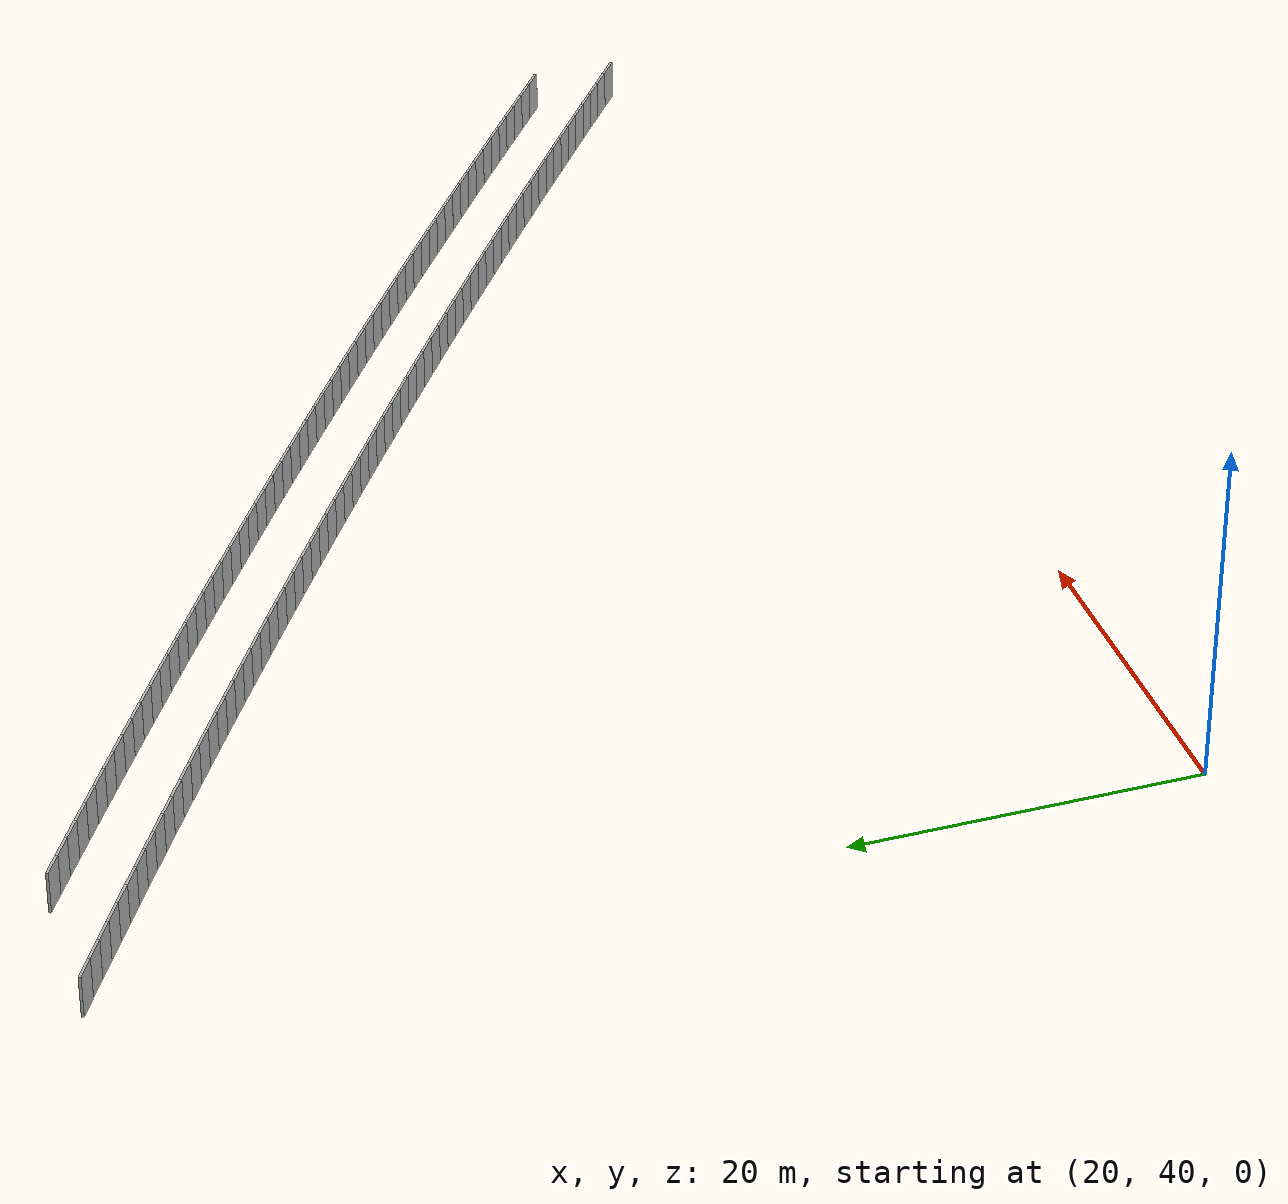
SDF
<?xml version="1.0" ?>
<sdf version="1.6">
  <model name="sps_1821">
    <pose frame="">0 0 0 0 -0 0</pose>
    <static>1</static>
    <self_collide>0</self_collide>
    <allow_auto_disable>0</allow_auto_disable>
    <link name="Wall10553">
      <kinematic>0</kinematic>
      <gravity>1</gravity>
      <self_collide>0</self_collide>
      <collision name="collision">
        <geometry>
          <box>
            <size>1.49647 0.15 2.5</size>
          </box>
        </geometry>
        <pose frame="">0 0 0 0 -0 0</pose>
      </collision>
      <visual name="visual">
        <geometry>
          <box>
            <size>1.49647 0.15 2.5</size>
          </box>
        </geometry>
        <pose frame="">0 0 0 0 -0 0</pose>
        <cast_shadows>1</cast_shadows>
        <transparency>0.0</transparency>
      </visual>
      <pose frame="">99.5561 47.0121 1.25 0 -0 2.50728</pose>
    </link>
    <link name="Wall10554">
      <kinematic>0</kinematic>
      <gravity>1</gravity>
      <self_collide>0</self_collide>
      <collision name="collision">
        <geometry>
          <box>
            <size>1.49649 0.15 2.5</size>
          </box>
        </geometry>
        <pose frame="">0 0 0 0 -0 0</pose>
      </collision>
      <visual name="visual">
        <geometry>
          <box>
            <size>1.49649 0.15 2.5</size>
          </box>
        </geometry>
        <pose frame="">0 0 0 0 -0 0</pose>
        <cast_shadows>1</cast_shadows>
        <transparency>0.0</transparency>
      </visual>
      <pose frame="">98.3501 47.898 1.25 0 -0 2.50886</pose>
    </link>
    <link name="Wall10555">
      <kinematic>0</kinematic>
      <gravity>1</gravity>
      <self_collide>0</self_collide>
      <collision name="collision">
        <geometry>
          <box>
            <size>1.49661 0.15 2.5</size>
          </box>
        </geometry>
        <pose frame="">0 0 0 0 -0 0</pose>
      </collision>
      <visual name="visual">
        <geometry>
          <box>
            <size>1.49661 0.15 2.5</size>
          </box>
        </geometry>
        <pose frame="">0 0 0 0 -0 0</pose>
        <cast_shadows>1</cast_shadows>
        <transparency>0.0</transparency>
      </visual>
      <pose frame="">97.1426 48.7821 1.25 0 -0 2.51033</pose>
    </link>
    <link name="Wall10556">
      <kinematic>0</kinematic>
      <gravity>1</gravity>
      <self_collide>0</self_collide>
      <collision name="collision">
        <geometry>
          <box>
            <size>1.49652 0.15 2.5</size>
          </box>
        </geometry>
        <pose frame="">0 0 0 0 -0 0</pose>
      </collision>
      <visual name="visual">
        <geometry>
          <box>
            <size>1.49652 0.15 2.5</size>
          </box>
        </geometry>
        <pose frame="">0 0 0 0 -0 0</pose>
        <cast_shadows>1</cast_shadows>
        <transparency>0.0</transparency>
      </visual>
      <pose frame="">95.9337 49.6643 1.25 0 -0 2.51201</pose>
    </link>
    <link name="Wall10557">
      <kinematic>0</kinematic>
      <gravity>1</gravity>
      <self_collide>0</self_collide>
      <collision name="collision">
        <geometry>
          <box>
            <size>1.49651 0.15 2.5</size>
          </box>
        </geometry>
        <pose frame="">0 0 0 0 -0 0</pose>
      </collision>
      <visual name="visual">
        <geometry>
          <box>
            <size>1.49651 0.15 2.5</size>
          </box>
        </geometry>
        <pose frame="">0 0 0 0 -0 0</pose>
        <cast_shadows>1</cast_shadows>
        <transparency>0.0</transparency>
      </visual>
      <pose frame="">94.7234 50.5445 1.25 0 -0 2.51361</pose>
    </link>
    <link name="Wall10558">
      <kinematic>0</kinematic>
      <gravity>1</gravity>
      <self_collide>0</self_collide>
      <collision name="collision">
        <geometry>
          <box>
            <size>1.49657 0.15 2.5</size>
          </box>
        </geometry>
        <pose frame="">0 0 0 0 -0 0</pose>
      </collision>
      <visual name="visual">
        <geometry>
          <box>
            <size>1.49657 0.15 2.5</size>
          </box>
        </geometry>
        <pose frame="">0 0 0 0 -0 0</pose>
        <cast_shadows>1</cast_shadows>
        <transparency>0.0</transparency>
      </visual>
      <pose frame="">93.5117 51.4228 1.25 0 -0 2.51516</pose>
    </link>
    <link name="Wall10559">
      <kinematic>0</kinematic>
      <gravity>1</gravity>
      <self_collide>0</self_collide>
      <collision name="collision">
        <geometry>
          <box>
            <size>1.49641 0.15 2.5</size>
          </box>
        </geometry>
        <pose frame="">0 0 0 0 -0 0</pose>
      </collision>
      <visual name="visual">
        <geometry>
          <box>
            <size>1.49641 0.15 2.5</size>
          </box>
        </geometry>
        <pose frame="">0 0 0 0 -0 0</pose>
        <cast_shadows>1</cast_shadows>
        <transparency>0.0</transparency>
      </visual>
      <pose frame="">92.2987 52.2992 1.25 0 -0 2.51669</pose>
    </link>
    <link name="Wall10560">
      <kinematic>0</kinematic>
      <gravity>1</gravity>
      <self_collide>0</self_collide>
      <collision name="collision">
        <geometry>
          <box>
            <size>1.49652 0.15 2.5</size>
          </box>
        </geometry>
        <pose frame="">0 0 0 0 -0 0</pose>
      </collision>
      <visual name="visual">
        <geometry>
          <box>
            <size>1.49652 0.15 2.5</size>
          </box>
        </geometry>
        <pose frame="">0 0 0 0 -0 0</pose>
        <cast_shadows>1</cast_shadows>
        <transparency>0.0</transparency>
      </visual>
      <pose frame="">91.0843 53.1736 1.25 0 -0 2.5184</pose>
    </link>
    <link name="Wall10561">
      <kinematic>0</kinematic>
      <gravity>1</gravity>
      <self_collide>0</self_collide>
      <collision name="collision">
        <geometry>
          <box>
            <size>1.4966 0.15 2.5</size>
          </box>
        </geometry>
        <pose frame="">0 0 0 0 -0 0</pose>
      </collision>
      <visual name="visual">
        <geometry>
          <box>
            <size>1.4966 0.15 2.5</size>
          </box>
        </geometry>
        <pose frame="">0 0 0 0 -0 0</pose>
        <cast_shadows>1</cast_shadows>
        <transparency>0.0</transparency>
      </visual>
      <pose frame="">89.8683 54.0461 1.25 0 -0 2.51994</pose>
    </link>
    <link name="Wall10562">
      <kinematic>0</kinematic>
      <gravity>1</gravity>
      <self_collide>0</self_collide>
      <collision name="collision">
        <geometry>
          <box>
            <size>1.4964 0.15 2.5</size>
          </box>
        </geometry>
        <pose frame="">0 0 0 0 -0 0</pose>
      </collision>
      <visual name="visual">
        <geometry>
          <box>
            <size>1.4964 0.15 2.5</size>
          </box>
        </geometry>
        <pose frame="">0 0 0 0 -0 0</pose>
        <cast_shadows>1</cast_shadows>
        <transparency>0.0</transparency>
      </visual>
      <pose frame="">88.6511 54.9167 1.25 0 -0 2.52146</pose>
    </link>
    <link name="Wall10563">
      <kinematic>0</kinematic>
      <gravity>1</gravity>
      <self_collide>0</self_collide>
      <collision name="collision">
        <geometry>
          <box>
            <size>1.49654 0.15 2.5</size>
          </box>
        </geometry>
        <pose frame="">0 0 0 0 -0 0</pose>
      </collision>
      <visual name="visual">
        <geometry>
          <box>
            <size>1.49654 0.15 2.5</size>
          </box>
        </geometry>
        <pose frame="">0 0 0 0 -0 0</pose>
        <cast_shadows>1</cast_shadows>
        <transparency>0.0</transparency>
      </visual>
      <pose frame="">87.4325 55.7853 1.25 0 -0 2.52323</pose>
    </link>
    <link name="Wall10564">
      <kinematic>0</kinematic>
      <gravity>1</gravity>
      <self_collide>0</self_collide>
      <collision name="collision">
        <geometry>
          <box>
            <size>1.49656 0.15 2.5</size>
          </box>
        </geometry>
        <pose frame="">0 0 0 0 -0 0</pose>
      </collision>
      <visual name="visual">
        <geometry>
          <box>
            <size>1.49656 0.15 2.5</size>
          </box>
        </geometry>
        <pose frame="">0 0 0 0 -0 0</pose>
        <cast_shadows>1</cast_shadows>
        <transparency>0.0</transparency>
      </visual>
      <pose frame="">86.2126 56.6522 1.25 0 -0 2.52433</pose>
    </link>
    <link name="Wall10565">
      <kinematic>0</kinematic>
      <gravity>1</gravity>
      <self_collide>0</self_collide>
      <collision name="collision">
        <geometry>
          <box>
            <size>1.49648 0.15 2.5</size>
          </box>
        </geometry>
        <pose frame="">0 0 0 0 -0 0</pose>
      </collision>
      <visual name="visual">
        <geometry>
          <box>
            <size>1.49648 0.15 2.5</size>
          </box>
        </geometry>
        <pose frame="">0 0 0 0 -0 0</pose>
        <cast_shadows>1</cast_shadows>
        <transparency>0.0</transparency>
      </visual>
      <pose frame="">84.9914 57.5172 1.25 0 -0 2.52625</pose>
    </link>
    <link name="Wall10566">
      <kinematic>0</kinematic>
      <gravity>1</gravity>
      <self_collide>0</self_collide>
      <collision name="collision">
        <geometry>
          <box>
            <size>1.49657 0.15 2.5</size>
          </box>
        </geometry>
        <pose frame="">0 0 0 0 -0 0</pose>
      </collision>
      <visual name="visual">
        <geometry>
          <box>
            <size>1.49657 0.15 2.5</size>
          </box>
        </geometry>
        <pose frame="">0 0 0 0 -0 0</pose>
        <cast_shadows>1</cast_shadows>
        <transparency>0.0</transparency>
      </visual>
      <pose frame="">83.7688 58.3801 1.25 0 -0 2.52779</pose>
    </link>
    <link name="Wall10567">
      <kinematic>0</kinematic>
      <gravity>1</gravity>
      <self_collide>0</self_collide>
      <collision name="collision">
        <geometry>
          <box>
            <size>1.49645 0.15 2.5</size>
          </box>
        </geometry>
        <pose frame="">0 0 0 0 -0 0</pose>
      </collision>
      <visual name="visual">
        <geometry>
          <box>
            <size>1.49645 0.15 2.5</size>
          </box>
        </geometry>
        <pose frame="">0 0 0 0 -0 0</pose>
        <cast_shadows>1</cast_shadows>
        <transparency>0.0</transparency>
      </visual>
      <pose frame="">82.5447 59.241 1.25 0 -0 2.52953</pose>
    </link>
    <link name="Wall10568">
      <kinematic>0</kinematic>
      <gravity>1</gravity>
      <self_collide>0</self_collide>
      <collision name="collision">
        <geometry>
          <box>
            <size>1.49651 0.15 2.5</size>
          </box>
        </geometry>
        <pose frame="">0 0 0 0 -0 0</pose>
      </collision>
      <visual name="visual">
        <geometry>
          <box>
            <size>1.49651 0.15 2.5</size>
          </box>
        </geometry>
        <pose frame="">0 0 0 0 -0 0</pose>
        <cast_shadows>1</cast_shadows>
        <transparency>0.0</transparency>
      </visual>
      <pose frame="">81.3193 60.1 1.25 0 -0 2.5309</pose>
    </link>
    <link name="Wall10569">
      <kinematic>0</kinematic>
      <gravity>1</gravity>
      <self_collide>0</self_collide>
      <collision name="collision">
        <geometry>
          <box>
            <size>1.49659 0.15 2.5</size>
          </box>
        </geometry>
        <pose frame="">0 0 0 0 -0 0</pose>
      </collision>
      <visual name="visual">
        <geometry>
          <box>
            <size>1.49659 0.15 2.5</size>
          </box>
        </geometry>
        <pose frame="">0 0 0 0 -0 0</pose>
        <cast_shadows>1</cast_shadows>
        <transparency>0.0</transparency>
      </visual>
      <pose frame="">80.0925 60.9571 1.25 0 -0 2.53267</pose>
    </link>
    <link name="Wall10570">
      <kinematic>0</kinematic>
      <gravity>1</gravity>
      <self_collide>0</self_collide>
      <collision name="collision">
        <geometry>
          <box>
            <size>1.49644 0.15 2.5</size>
          </box>
        </geometry>
        <pose frame="">0 0 0 0 -0 0</pose>
      </collision>
      <visual name="visual">
        <geometry>
          <box>
            <size>1.49644 0.15 2.5</size>
          </box>
        </geometry>
        <pose frame="">0 0 0 0 -0 0</pose>
        <cast_shadows>1</cast_shadows>
        <transparency>0.0</transparency>
      </visual>
      <pose frame="">78.8642 61.8121 1.25 0 -0 2.53424</pose>
    </link>
    <link name="Wall10571">
      <kinematic>0</kinematic>
      <gravity>1</gravity>
      <self_collide>0</self_collide>
      <collision name="collision">
        <geometry>
          <box>
            <size>1.49653 0.15 2.5</size>
          </box>
        </geometry>
        <pose frame="">0 0 0 0 -0 0</pose>
      </collision>
      <visual name="visual">
        <geometry>
          <box>
            <size>1.49653 0.15 2.5</size>
          </box>
        </geometry>
        <pose frame="">0 0 0 0 -0 0</pose>
        <cast_shadows>1</cast_shadows>
        <transparency>0.0</transparency>
      </visual>
      <pose frame="">77.6348 62.6652 1.25 0 -0 2.53573</pose>
    </link>
    <link name="Wall10572">
      <kinematic>0</kinematic>
      <gravity>1</gravity>
      <self_collide>0</self_collide>
      <collision name="collision">
        <geometry>
          <box>
            <size>1.4964 0.15 2.5</size>
          </box>
        </geometry>
        <pose frame="">0 0 0 0 -0 0</pose>
      </collision>
      <visual name="visual">
        <geometry>
          <box>
            <size>1.4964 0.15 2.5</size>
          </box>
        </geometry>
        <pose frame="">0 0 0 0 -0 0</pose>
        <cast_shadows>1</cast_shadows>
        <transparency>0.0</transparency>
      </visual>
      <pose frame="">76.404 63.5164 1.25 0 -0 2.53736</pose>
    </link>
    <link name="Wall10573">
      <kinematic>0</kinematic>
      <gravity>1</gravity>
      <self_collide>0</self_collide>
      <collision name="collision">
        <geometry>
          <box>
            <size>1.49655 0.15 2.5</size>
          </box>
        </geometry>
        <pose frame="">0 0 0 0 -0 0</pose>
      </collision>
      <visual name="visual">
        <geometry>
          <box>
            <size>1.49655 0.15 2.5</size>
          </box>
        </geometry>
        <pose frame="">0 0 0 0 -0 0</pose>
        <cast_shadows>1</cast_shadows>
        <transparency>0.0</transparency>
      </visual>
      <pose frame="">75.1717 64.3656 1.25 0 -0 2.53901</pose>
    </link>
    <link name="Wall10574">
      <kinematic>0</kinematic>
      <gravity>1</gravity>
      <self_collide>0</self_collide>
      <collision name="collision">
        <geometry>
          <box>
            <size>1.49656 0.15 2.5</size>
          </box>
        </geometry>
        <pose frame="">0 0 0 0 -0 0</pose>
      </collision>
      <visual name="visual">
        <geometry>
          <box>
            <size>1.49656 0.15 2.5</size>
          </box>
        </geometry>
        <pose frame="">0 0 0 0 -0 0</pose>
        <cast_shadows>1</cast_shadows>
        <transparency>0.0</transparency>
      </visual>
      <pose frame="">73.9382 65.2129 1.25 0 -0 2.54045</pose>
    </link>
    <link name="Wall10575">
      <kinematic>0</kinematic>
      <gravity>1</gravity>
      <self_collide>0</self_collide>
      <collision name="collision">
        <geometry>
          <box>
            <size>1.49654 0.15 2.5</size>
          </box>
        </geometry>
        <pose frame="">0 0 0 0 -0 0</pose>
      </collision>
      <visual name="visual">
        <geometry>
          <box>
            <size>1.49654 0.15 2.5</size>
          </box>
        </geometry>
        <pose frame="">0 0 0 0 -0 0</pose>
        <cast_shadows>1</cast_shadows>
        <transparency>0.0</transparency>
      </visual>
      <pose frame="">72.7033 66.0583 1.25 0 -0 2.54212</pose>
    </link>
    <link name="Wall10576">
      <kinematic>0</kinematic>
      <gravity>1</gravity>
      <self_collide>0</self_collide>
      <collision name="collision">
        <geometry>
          <box>
            <size>1.49645 0.15 2.5</size>
          </box>
        </geometry>
        <pose frame="">0 0 0 0 -0 0</pose>
      </collision>
      <visual name="visual">
        <geometry>
          <box>
            <size>1.49645 0.15 2.5</size>
          </box>
        </geometry>
        <pose frame="">0 0 0 0 -0 0</pose>
        <cast_shadows>1</cast_shadows>
        <transparency>0.0</transparency>
      </visual>
      <pose frame="">71.4671 66.9017 1.25 0 -0 2.54366</pose>
    </link>
    <link name="Wall10577">
      <kinematic>0</kinematic>
      <gravity>1</gravity>
      <self_collide>0</self_collide>
      <collision name="collision">
        <geometry>
          <box>
            <size>1.49648 0.15 2.5</size>
          </box>
        </geometry>
        <pose frame="">0 0 0 0 -0 0</pose>
      </collision>
      <visual name="visual">
        <geometry>
          <box>
            <size>1.49648 0.15 2.5</size>
          </box>
        </geometry>
        <pose frame="">0 0 0 0 -0 0</pose>
        <cast_shadows>1</cast_shadows>
        <transparency>0.0</transparency>
      </visual>
      <pose frame="">70.2295 67.7431 1.25 0 -0 2.5453</pose>
    </link>
    <link name="Wall10578">
      <kinematic>0</kinematic>
      <gravity>1</gravity>
      <self_collide>0</self_collide>
      <collision name="collision">
        <geometry>
          <box>
            <size>1.4965 0.15 2.5</size>
          </box>
        </geometry>
        <pose frame="">0 0 0 0 -0 0</pose>
      </collision>
      <visual name="visual">
        <geometry>
          <box>
            <size>1.4965 0.15 2.5</size>
          </box>
        </geometry>
        <pose frame="">0 0 0 0 -0 0</pose>
        <cast_shadows>1</cast_shadows>
        <transparency>0.0</transparency>
      </visual>
      <pose frame="">68.9907 68.5825 1.25 0 -0 2.54688</pose>
    </link>
    <link name="Wall10579">
      <kinematic>0</kinematic>
      <gravity>1</gravity>
      <self_collide>0</self_collide>
      <collision name="collision">
        <geometry>
          <box>
            <size>1.49665 0.15 2.5</size>
          </box>
        </geometry>
        <pose frame="">0 0 0 0 -0 0</pose>
      </collision>
      <visual name="visual">
        <geometry>
          <box>
            <size>1.49665 0.15 2.5</size>
          </box>
        </geometry>
        <pose frame="">0 0 0 0 -0 0</pose>
        <cast_shadows>1</cast_shadows>
        <transparency>0.0</transparency>
      </visual>
      <pose frame="">67.7504 69.42 1.25 0 -0 2.54848</pose>
    </link>
    <link name="Wall10580">
      <kinematic>0</kinematic>
      <gravity>1</gravity>
      <self_collide>0</self_collide>
      <collision name="collision">
        <geometry>
          <box>
            <size>1.49642 0.15 2.5</size>
          </box>
        </geometry>
        <pose frame="">0 0 0 0 -0 0</pose>
      </collision>
      <visual name="visual">
        <geometry>
          <box>
            <size>1.49642 0.15 2.5</size>
          </box>
        </geometry>
        <pose frame="">0 0 0 0 -0 0</pose>
        <cast_shadows>1</cast_shadows>
        <transparency>0.0</transparency>
      </visual>
      <pose frame="">66.5088 70.2555 1.25 0 -0 2.55009</pose>
    </link>
    <link name="Wall10581">
      <kinematic>0</kinematic>
      <gravity>1</gravity>
      <self_collide>0</self_collide>
      <collision name="collision">
        <geometry>
          <box>
            <size>1.49641 0.15 2.5</size>
          </box>
        </geometry>
        <pose frame="">0 0 0 0 -0 0</pose>
      </collision>
      <visual name="visual">
        <geometry>
          <box>
            <size>1.49641 0.15 2.5</size>
          </box>
        </geometry>
        <pose frame="">0 0 0 0 -0 0</pose>
        <cast_shadows>1</cast_shadows>
        <transparency>0.0</transparency>
      </visual>
      <pose frame="">65.266 71.089 1.25 0 -0 2.55157</pose>
    </link>
    <link name="Wall10582">
      <kinematic>0</kinematic>
      <gravity>1</gravity>
      <self_collide>0</self_collide>
      <collision name="collision">
        <geometry>
          <box>
            <size>1.49673 0.15 2.5</size>
          </box>
        </geometry>
        <pose frame="">0 0 0 0 -0 0</pose>
      </collision>
      <visual name="visual">
        <geometry>
          <box>
            <size>1.49673 0.15 2.5</size>
          </box>
        </geometry>
        <pose frame="">0 0 0 0 -0 0</pose>
        <cast_shadows>1</cast_shadows>
        <transparency>0.0</transparency>
      </visual>
      <pose frame="">64.0218 71.9208 1.25 0 -0 2.55293</pose>
    </link>
    <link name="Wall10583">
      <kinematic>0</kinematic>
      <gravity>1</gravity>
      <self_collide>0</self_collide>
      <collision name="collision">
        <geometry>
          <box>
            <size>1.49631 0.15 2.5</size>
          </box>
        </geometry>
        <pose frame="">0 0 0 0 -0 0</pose>
      </collision>
      <visual name="visual">
        <geometry>
          <box>
            <size>1.49631 0.15 2.5</size>
          </box>
        </geometry>
        <pose frame="">0 0 0 0 -0 0</pose>
        <cast_shadows>1</cast_shadows>
        <transparency>0.0</transparency>
      </visual>
      <pose frame="">62.7765 72.7506 1.25 0 -0 2.55476</pose>
    </link>
    <link name="Wall10584">
      <kinematic>0</kinematic>
      <gravity>1</gravity>
      <self_collide>0</self_collide>
      <collision name="collision">
        <geometry>
          <box>
            <size>1.49659 0.15 2.5</size>
          </box>
        </geometry>
        <pose frame="">0 0 0 0 -0 0</pose>
      </collision>
      <visual name="visual">
        <geometry>
          <box>
            <size>1.49659 0.15 2.5</size>
          </box>
        </geometry>
        <pose frame="">0 0 0 0 -0 0</pose>
        <cast_shadows>1</cast_shadows>
        <transparency>0.0</transparency>
      </visual>
      <pose frame="">61.5297 73.5783 1.25 0 -0 2.55625</pose>
    </link>
    <link name="Wall10585">
      <kinematic>0</kinematic>
      <gravity>1</gravity>
      <self_collide>0</self_collide>
      <collision name="collision">
        <geometry>
          <box>
            <size>1.49661 0.15 2.5</size>
          </box>
        </geometry>
        <pose frame="">0 0 0 0 -0 0</pose>
      </collision>
      <visual name="visual">
        <geometry>
          <box>
            <size>1.49661 0.15 2.5</size>
          </box>
        </geometry>
        <pose frame="">0 0 0 0 -0 0</pose>
        <cast_shadows>1</cast_shadows>
        <transparency>0.0</transparency>
      </visual>
      <pose frame="">60.2815 74.404 1.25 0 -0 2.55807</pose>
    </link>
    <link name="Wall10586">
      <kinematic>0</kinematic>
      <gravity>1</gravity>
      <self_collide>0</self_collide>
      <collision name="collision">
        <geometry>
          <box>
            <size>1.49637 0.15 2.5</size>
          </box>
        </geometry>
        <pose frame="">0 0 0 0 -0 0</pose>
      </collision>
      <visual name="visual">
        <geometry>
          <box>
            <size>1.49637 0.15 2.5</size>
          </box>
        </geometry>
        <pose frame="">0 0 0 0 -0 0</pose>
        <cast_shadows>1</cast_shadows>
        <transparency>0.0</transparency>
      </visual>
      <pose frame="">59.0321 75.2276 1.25 0 -0 2.55957</pose>
    </link>
    <link name="Wall10587">
      <kinematic>0</kinematic>
      <gravity>1</gravity>
      <self_collide>0</self_collide>
      <collision name="collision">
        <geometry>
          <box>
            <size>1.49657 0.15 2.5</size>
          </box>
        </geometry>
        <pose frame="">0 0 0 0 -0 0</pose>
      </collision>
      <visual name="visual">
        <geometry>
          <box>
            <size>1.49657 0.15 2.5</size>
          </box>
        </geometry>
        <pose frame="">0 0 0 0 -0 0</pose>
        <cast_shadows>1</cast_shadows>
        <transparency>0.0</transparency>
      </visual>
      <pose frame="">57.7814 76.0493 1.25 0 -0 2.56108</pose>
    </link>
    <link name="Wall10588">
      <kinematic>0</kinematic>
      <gravity>1</gravity>
      <self_collide>0</self_collide>
      <collision name="collision">
        <geometry>
          <box>
            <size>1.49654 0.15 2.5</size>
          </box>
        </geometry>
        <pose frame="">0 0 0 0 -0 0</pose>
      </collision>
      <visual name="visual">
        <geometry>
          <box>
            <size>1.49654 0.15 2.5</size>
          </box>
        </geometry>
        <pose frame="">0 0 0 0 -0 0</pose>
        <cast_shadows>1</cast_shadows>
        <transparency>0.0</transparency>
      </visual>
      <pose frame="">56.5293 76.869 1.25 0 -0 2.56282</pose>
    </link>
    <link name="Wall10589">
      <kinematic>0</kinematic>
      <gravity>1</gravity>
      <self_collide>0</self_collide>
      <collision name="collision">
        <geometry>
          <box>
            <size>1.4966 0.15 2.5</size>
          </box>
        </geometry>
        <pose frame="">0 0 0 0 -0 0</pose>
      </collision>
      <visual name="visual">
        <geometry>
          <box>
            <size>1.4966 0.15 2.5</size>
          </box>
        </geometry>
        <pose frame="">0 0 0 0 -0 0</pose>
        <cast_shadows>1</cast_shadows>
        <transparency>0.0</transparency>
      </visual>
      <pose frame="">55.2758 77.6867 1.25 0 -0 2.56426</pose>
    </link>
    <link name="Wall10590">
      <kinematic>0</kinematic>
      <gravity>1</gravity>
      <self_collide>0</self_collide>
      <collision name="collision">
        <geometry>
          <box>
            <size>1.49644 0.15 2.5</size>
          </box>
        </geometry>
        <pose frame="">0 0 0 0 -0 0</pose>
      </collision>
      <visual name="visual">
        <geometry>
          <box>
            <size>1.49644 0.15 2.5</size>
          </box>
        </geometry>
        <pose frame="">0 0 0 0 -0 0</pose>
        <cast_shadows>1</cast_shadows>
        <transparency>0.0</transparency>
      </visual>
      <pose frame="">54.0212 78.5025 1.25 0 -0 2.56584</pose>
    </link>
    <link name="Wall10591">
      <kinematic>0</kinematic>
      <gravity>1</gravity>
      <self_collide>0</self_collide>
      <collision name="collision">
        <geometry>
          <box>
            <size>1.49655 0.15 2.5</size>
          </box>
        </geometry>
        <pose frame="">0 0 0 0 -0 0</pose>
      </collision>
      <visual name="visual">
        <geometry>
          <box>
            <size>1.49655 0.15 2.5</size>
          </box>
        </geometry>
        <pose frame="">0 0 0 0 -0 0</pose>
        <cast_shadows>1</cast_shadows>
        <transparency>0.0</transparency>
      </visual>
      <pose frame="">52.7653 79.3163 1.25 0 -0 2.56745</pose>
    </link>
    <link name="Wall10592">
      <kinematic>0</kinematic>
      <gravity>1</gravity>
      <self_collide>0</self_collide>
      <collision name="collision">
        <geometry>
          <box>
            <size>1.49652 0.15 2.5</size>
          </box>
        </geometry>
        <pose frame="">0 0 0 0 -0 0</pose>
      </collision>
      <visual name="visual">
        <geometry>
          <box>
            <size>1.49652 0.15 2.5</size>
          </box>
        </geometry>
        <pose frame="">0 0 0 0 -0 0</pose>
        <cast_shadows>1</cast_shadows>
        <transparency>0.0</transparency>
      </visual>
      <pose frame="">51.5081 80.1281 1.25 0 -0 2.56899</pose>
    </link>
    <link name="Wall10593">
      <kinematic>0</kinematic>
      <gravity>1</gravity>
      <self_collide>0</self_collide>
      <collision name="collision">
        <geometry>
          <box>
            <size>1.49643 0.15 2.5</size>
          </box>
        </geometry>
        <pose frame="">0 0 0 0 -0 0</pose>
      </collision>
      <visual name="visual">
        <geometry>
          <box>
            <size>1.49643 0.15 2.5</size>
          </box>
        </geometry>
        <pose frame="">0 0 0 0 -0 0</pose>
        <cast_shadows>1</cast_shadows>
        <transparency>0.0</transparency>
      </visual>
      <pose frame="">50.2497 80.9378 1.25 0 -0 2.57074</pose>
    </link>
    <link name="Wall10594">
      <kinematic>0</kinematic>
      <gravity>1</gravity>
      <self_collide>0</self_collide>
      <collision name="collision">
        <geometry>
          <box>
            <size>1.49652 0.15 2.5</size>
          </box>
        </geometry>
        <pose frame="">0 0 0 0 -0 0</pose>
      </collision>
      <visual name="visual">
        <geometry>
          <box>
            <size>1.49652 0.15 2.5</size>
          </box>
        </geometry>
        <pose frame="">0 0 0 0 -0 0</pose>
        <cast_shadows>1</cast_shadows>
        <transparency>0.0</transparency>
      </visual>
      <pose frame="">48.9899 81.7455 1.25 0 -0 2.57223</pose>
    </link>
    <link name="Wall10595">
      <kinematic>0</kinematic>
      <gravity>1</gravity>
      <self_collide>0</self_collide>
      <collision name="collision">
        <geometry>
          <box>
            <size>1.49654 0.15 2.5</size>
          </box>
        </geometry>
        <pose frame="">0 0 0 0 -0 0</pose>
      </collision>
      <visual name="visual">
        <geometry>
          <box>
            <size>1.49654 0.15 2.5</size>
          </box>
        </geometry>
        <pose frame="">0 0 0 0 -0 0</pose>
        <cast_shadows>1</cast_shadows>
        <transparency>0.0</transparency>
      </visual>
      <pose frame="">47.7288 82.5514 1.25 0 -0 2.57365</pose>
    </link>
    <link name="Wall10596">
      <kinematic>0</kinematic>
      <gravity>1</gravity>
      <self_collide>0</self_collide>
      <collision name="collision">
        <geometry>
          <box>
            <size>1.49655 0.15 2.5</size>
          </box>
        </geometry>
        <pose frame="">0 0 0 0 -0 0</pose>
      </collision>
      <visual name="visual">
        <geometry>
          <box>
            <size>1.49655 0.15 2.5</size>
          </box>
        </geometry>
        <pose frame="">0 0 0 0 -0 0</pose>
        <cast_shadows>1</cast_shadows>
        <transparency>0.0</transparency>
      </visual>
      <pose frame="">46.4665 83.3553 1.25 0 -0 2.57539</pose>
    </link>
    <link name="Wall10597">
      <kinematic>0</kinematic>
      <gravity>1</gravity>
      <self_collide>0</self_collide>
      <collision name="collision">
        <geometry>
          <box>
            <size>1.49669 0.15 2.5</size>
          </box>
        </geometry>
        <pose frame="">0 0 0 0 -0 0</pose>
      </collision>
      <visual name="visual">
        <geometry>
          <box>
            <size>1.49669 0.15 2.5</size>
          </box>
        </geometry>
        <pose frame="">0 0 0 0 -0 0</pose>
        <cast_shadows>1</cast_shadows>
        <transparency>0.0</transparency>
      </visual>
      <pose frame="">45.2028 84.1571 1.25 0 -0 2.57699</pose>
    </link>
    <link name="Wall10598">
      <kinematic>0</kinematic>
      <gravity>1</gravity>
      <self_collide>0</self_collide>
      <collision name="collision">
        <geometry>
          <box>
            <size>1.4964 0.15 2.5</size>
          </box>
        </geometry>
        <pose frame="">0 0 0 0 -0 0</pose>
      </collision>
      <visual name="visual">
        <geometry>
          <box>
            <size>1.4964 0.15 2.5</size>
          </box>
        </geometry>
        <pose frame="">0 0 0 0 -0 0</pose>
        <cast_shadows>1</cast_shadows>
        <transparency>0.0</transparency>
      </visual>
      <pose frame="">43.9379 84.9569 1.25 0 -0 2.57851</pose>
    </link>
    <link name="Wall10599">
      <kinematic>0</kinematic>
      <gravity>1</gravity>
      <self_collide>0</self_collide>
      <collision name="collision">
        <geometry>
          <box>
            <size>1.49655 0.15 2.5</size>
          </box>
        </geometry>
        <pose frame="">0 0 0 0 -0 0</pose>
      </collision>
      <visual name="visual">
        <geometry>
          <box>
            <size>1.49655 0.15 2.5</size>
          </box>
        </geometry>
        <pose frame="">0 0 0 0 -0 0</pose>
        <cast_shadows>1</cast_shadows>
        <transparency>0.0</transparency>
      </visual>
      <pose frame="">42.6719 85.7547 1.25 0 -0 2.58012</pose>
    </link>
    <link name="Wall10600">
      <kinematic>0</kinematic>
      <gravity>1</gravity>
      <self_collide>0</self_collide>
      <collision name="collision">
        <geometry>
          <box>
            <size>1.49645 0.15 2.5</size>
          </box>
        </geometry>
        <pose frame="">0 0 0 0 -0 0</pose>
      </collision>
      <visual name="visual">
        <geometry>
          <box>
            <size>1.49645 0.15 2.5</size>
          </box>
        </geometry>
        <pose frame="">0 0 0 0 -0 0</pose>
        <cast_shadows>1</cast_shadows>
        <transparency>0.0</transparency>
      </visual>
      <pose frame="">41.4046 86.5506 1.25 0 -0 2.58152</pose>
    </link>
    <link name="Wall10601">
      <kinematic>0</kinematic>
      <gravity>1</gravity>
      <self_collide>0</self_collide>
      <collision name="collision">
        <geometry>
          <box>
            <size>1.49666 0.15 2.5</size>
          </box>
        </geometry>
        <pose frame="">0 0 0 0 -0 0</pose>
      </collision>
      <visual name="visual">
        <geometry>
          <box>
            <size>1.49666 0.15 2.5</size>
          </box>
        </geometry>
        <pose frame="">0 0 0 0 -0 0</pose>
        <cast_shadows>1</cast_shadows>
        <transparency>0.0</transparency>
      </visual>
      <pose frame="">40.1359 87.3445 1.25 0 -0 2.5833</pose>
    </link>
    <link name="Wall10602">
      <kinematic>0</kinematic>
      <gravity>1</gravity>
      <self_collide>0</self_collide>
      <collision name="collision">
        <geometry>
          <box>
            <size>1.4964 0.15 2.5</size>
          </box>
        </geometry>
        <pose frame="">0 0 0 0 -0 0</pose>
      </collision>
      <visual name="visual">
        <geometry>
          <box>
            <size>1.4964 0.15 2.5</size>
          </box>
        </geometry>
        <pose frame="">0 0 0 0 -0 0</pose>
        <cast_shadows>1</cast_shadows>
        <transparency>0.0</transparency>
      </visual>
      <pose frame="">38.8661 88.1363 1.25 0 -0 2.58482</pose>
    </link>
    <link name="Wall10603">
      <kinematic>0</kinematic>
      <gravity>1</gravity>
      <self_collide>0</self_collide>
      <collision name="collision">
        <geometry>
          <box>
            <size>1.49643 0.15 2.5</size>
          </box>
        </geometry>
        <pose frame="">0 0 0 0 -0 0</pose>
      </collision>
      <visual name="visual">
        <geometry>
          <box>
            <size>1.49643 0.15 2.5</size>
          </box>
        </geometry>
        <pose frame="">0 0 0 0 -0 0</pose>
        <cast_shadows>1</cast_shadows>
        <transparency>0.0</transparency>
      </visual>
      <pose frame="">37.595 88.926 1.25 0 -0 2.58656</pose>
    </link>
    <link name="Wall10604">
      <kinematic>0</kinematic>
      <gravity>1</gravity>
      <self_collide>0</self_collide>
      <collision name="collision">
        <geometry>
          <box>
            <size>1.49669 0.15 2.5</size>
          </box>
        </geometry>
        <pose frame="">0 0 0 0 -0 0</pose>
      </collision>
      <visual name="visual">
        <geometry>
          <box>
            <size>1.49669 0.15 2.5</size>
          </box>
        </geometry>
        <pose frame="">0 0 0 0 -0 0</pose>
        <cast_shadows>1</cast_shadows>
        <transparency>0.0</transparency>
      </visual>
      <pose frame="">36.3225 89.7137 1.25 0 -0 2.58806</pose>
    </link>
    <link name="Wall10605">
      <kinematic>0</kinematic>
      <gravity>1</gravity>
      <self_collide>0</self_collide>
      <collision name="collision">
        <geometry>
          <box>
            <size>1.49642 0.15 2.5</size>
          </box>
        </geometry>
        <pose frame="">0 0 0 0 -0 0</pose>
      </collision>
      <visual name="visual">
        <geometry>
          <box>
            <size>1.49642 0.15 2.5</size>
          </box>
        </geometry>
        <pose frame="">0 0 0 0 -0 0</pose>
        <cast_shadows>1</cast_shadows>
        <transparency>0.0</transparency>
      </visual>
      <pose frame="">35.0488 90.4994 1.25 0 -0 2.58967</pose>
    </link>
    <link name="Wall10606">
      <kinematic>0</kinematic>
      <gravity>1</gravity>
      <self_collide>0</self_collide>
      <collision name="collision">
        <geometry>
          <box>
            <size>1.49635 0.15 2.5</size>
          </box>
        </geometry>
        <pose frame="">0 0 0 0 -0 0</pose>
      </collision>
      <visual name="visual">
        <geometry>
          <box>
            <size>1.49635 0.15 2.5</size>
          </box>
        </geometry>
        <pose frame="">0 0 0 0 -0 0</pose>
        <cast_shadows>1</cast_shadows>
        <transparency>0.0</transparency>
      </visual>
      <pose frame="">33.7739 91.283 1.25 0 -0 2.59123</pose>
    </link>
    <link name="Wall10607">
      <kinematic>0</kinematic>
      <gravity>1</gravity>
      <self_collide>0</self_collide>
      <collision name="collision">
        <geometry>
          <box>
            <size>1.49663 0.15 2.5</size>
          </box>
        </geometry>
        <pose frame="">0 0 0 0 -0 0</pose>
      </collision>
      <visual name="visual">
        <geometry>
          <box>
            <size>1.49663 0.15 2.5</size>
          </box>
        </geometry>
        <pose frame="">0 0 0 0 -0 0</pose>
        <cast_shadows>1</cast_shadows>
        <transparency>0.0</transparency>
      </visual>
      <pose frame="">32.4979 92.0647 1.25 0 -0 2.59272</pose>
    </link>
    <link name="Wall10608">
      <kinematic>0</kinematic>
      <gravity>1</gravity>
      <self_collide>0</self_collide>
      <collision name="collision">
        <geometry>
          <box>
            <size>1.49652 0.15 2.5</size>
          </box>
        </geometry>
        <pose frame="">0 0 0 0 -0 0</pose>
      </collision>
      <visual name="visual">
        <geometry>
          <box>
            <size>1.49652 0.15 2.5</size>
          </box>
        </geometry>
        <pose frame="">0 0 0 0 -0 0</pose>
        <cast_shadows>1</cast_shadows>
        <transparency>0.0</transparency>
      </visual>
      <pose frame="">31.2205 92.8444 1.25 0 -0 2.5944</pose>
    </link>
    <link name="Wall10609">
      <kinematic>0</kinematic>
      <gravity>1</gravity>
      <self_collide>0</self_collide>
      <collision name="collision">
        <geometry>
          <box>
            <size>1.49659 0.15 2.5</size>
          </box>
        </geometry>
        <pose frame="">0 0 0 0 -0 0</pose>
      </collision>
      <visual name="visual">
        <geometry>
          <box>
            <size>1.49659 0.15 2.5</size>
          </box>
        </geometry>
        <pose frame="">0 0 0 0 -0 0</pose>
        <cast_shadows>1</cast_shadows>
        <transparency>0.0</transparency>
      </visual>
      <pose frame="">29.9418 93.622 1.25 0 -0 2.59605</pose>
    </link>
    <link name="Wall10610">
      <kinematic>0</kinematic>
      <gravity>1</gravity>
      <self_collide>0</self_collide>
      <collision name="collision">
        <geometry>
          <box>
            <size>1.49652 0.15 2.5</size>
          </box>
        </geometry>
        <pose frame="">0 0 0 0 -0 0</pose>
      </collision>
      <visual name="visual">
        <geometry>
          <box>
            <size>1.49652 0.15 2.5</size>
          </box>
        </geometry>
        <pose frame="">0 0 0 0 -0 0</pose>
        <cast_shadows>1</cast_shadows>
        <transparency>0.0</transparency>
      </visual>
      <pose frame="">28.6619 94.3976 1.25 0 -0 2.59755</pose>
    </link>
    <link name="Wall10611">
      <kinematic>0</kinematic>
      <gravity>1</gravity>
      <self_collide>0</self_collide>
      <collision name="collision">
        <geometry>
          <box>
            <size>1.49666 0.15 2.5</size>
          </box>
        </geometry>
        <pose frame="">0 0 0 0 -0 0</pose>
      </collision>
      <visual name="visual">
        <geometry>
          <box>
            <size>1.49666 0.15 2.5</size>
          </box>
        </geometry>
        <pose frame="">0 0 0 0 -0 0</pose>
        <cast_shadows>1</cast_shadows>
        <transparency>0.0</transparency>
      </visual>
      <pose frame="">27.3807 95.1712 1.25 0 -0 2.59913</pose>
    </link>
    <link name="Wall10612">
      <kinematic>0</kinematic>
      <gravity>1</gravity>
      <self_collide>0</self_collide>
      <collision name="collision">
        <geometry>
          <box>
            <size>1.49643 0.15 2.5</size>
          </box>
        </geometry>
        <pose frame="">0 0 0 0 -0 0</pose>
      </collision>
      <visual name="visual">
        <geometry>
          <box>
            <size>1.49643 0.15 2.5</size>
          </box>
        </geometry>
        <pose frame="">0 0 0 0 -0 0</pose>
        <cast_shadows>1</cast_shadows>
        <transparency>0.0</transparency>
      </visual>
      <pose frame="">26.0984 95.9428 1.25 0 -0 2.60066</pose>
    </link>
    <link name="Wall10613">
      <kinematic>0</kinematic>
      <gravity>1</gravity>
      <self_collide>0</self_collide>
      <collision name="collision">
        <geometry>
          <box>
            <size>1.49653 0.15 2.5</size>
          </box>
        </geometry>
        <pose frame="">0 0 0 0 -0 0</pose>
      </collision>
      <visual name="visual">
        <geometry>
          <box>
            <size>1.49653 0.15 2.5</size>
          </box>
        </geometry>
        <pose frame="">0 0 0 0 -0 0</pose>
        <cast_shadows>1</cast_shadows>
        <transparency>0.0</transparency>
      </visual>
      <pose frame="">24.815 96.7123 1.25 0 -0 2.60236</pose>
    </link>
    <link name="Wall10614">
      <kinematic>0</kinematic>
      <gravity>1</gravity>
      <self_collide>0</self_collide>
      <collision name="collision">
        <geometry>
          <box>
            <size>1.49636 0.15 2.5</size>
          </box>
        </geometry>
        <pose frame="">0 0 0 0 -0 0</pose>
      </collision>
      <visual name="visual">
        <geometry>
          <box>
            <size>1.49636 0.15 2.5</size>
          </box>
        </geometry>
        <pose frame="">0 0 0 0 -0 0</pose>
        <cast_shadows>1</cast_shadows>
        <transparency>0.0</transparency>
      </visual>
      <pose frame="">23.5303 97.4797 1.25 0 -0 2.60391</pose>
    </link>
    <link name="Wall10615">
      <kinematic>0</kinematic>
      <gravity>1</gravity>
      <self_collide>0</self_collide>
      <collision name="collision">
        <geometry>
          <box>
            <size>1.49657 0.15 2.5</size>
          </box>
        </geometry>
        <pose frame="">0 0 0 0 -0 0</pose>
      </collision>
      <visual name="visual">
        <geometry>
          <box>
            <size>1.49657 0.15 2.5</size>
          </box>
        </geometry>
        <pose frame="">0 0 0 0 -0 0</pose>
        <cast_shadows>1</cast_shadows>
        <transparency>0.0</transparency>
      </visual>
      <pose frame="">22.2443 98.2451 1.25 0 -0 2.60551</pose>
    </link>
    <link name="Wall10616">
      <kinematic>0</kinematic>
      <gravity>1</gravity>
      <self_collide>0</self_collide>
      <collision name="collision">
        <geometry>
          <box>
            <size>1.49644 0.15 2.5</size>
          </box>
        </geometry>
        <pose frame="">0 0 0 0 -0 0</pose>
      </collision>
      <visual name="visual">
        <geometry>
          <box>
            <size>1.49644 0.15 2.5</size>
          </box>
        </geometry>
        <pose frame="">0 0 0 0 -0 0</pose>
        <cast_shadows>1</cast_shadows>
        <transparency>0.0</transparency>
      </visual>
      <pose frame="">20.9571 99.0084 1.25 0 -0 2.60717</pose>
    </link>
    <link name="Wall10617">
      <kinematic>0</kinematic>
      <gravity>1</gravity>
      <self_collide>0</self_collide>
      <collision name="collision">
        <geometry>
          <box>
            <size>1.49659 0.15 2.5</size>
          </box>
        </geometry>
        <pose frame="">0 0 0 0 -0 0</pose>
      </collision>
      <visual name="visual">
        <geometry>
          <box>
            <size>1.49659 0.15 2.5</size>
          </box>
        </geometry>
        <pose frame="">0 0 0 0 -0 0</pose>
        <cast_shadows>1</cast_shadows>
        <transparency>0.0</transparency>
      </visual>
      <pose frame="">19.6688 99.7697 1.25 0 -0 2.6086</pose>
    </link>
    <link name="Wall11152">
      <kinematic>0</kinematic>
      <gravity>1</gravity>
      <self_collide>0</self_collide>
      <collision name="collision">
        <geometry>
          <box>
            <size>1.50303 0.15 2.5</size>
          </box>
        </geometry>
        <pose frame="">0 0 0 0 -0 0</pose>
      </collision>
      <visual name="visual">
        <geometry>
          <box>
            <size>1.50303 0.15 2.5</size>
          </box>
        </geometry>
        <pose frame="">0 0 0 0 -0 0</pose>
        <cast_shadows>1</cast_shadows>
        <transparency>0.0</transparency>
      </visual>
      <pose frame="">99.5853 52.1248 1.25 0 -0 2.51034</pose>
    </link>
    <link name="Wall11153">
      <kinematic>0</kinematic>
      <gravity>1</gravity>
      <self_collide>0</self_collide>
      <collision name="collision">
        <geometry>
          <box>
            <size>1.50317 0.15 2.5</size>
          </box>
        </geometry>
        <pose frame="">0 0 0 0 -0 0</pose>
      </collision>
      <visual name="visual">
        <geometry>
          <box>
            <size>1.50317 0.15 2.5</size>
          </box>
        </geometry>
        <pose frame="">0 0 0 0 -0 0</pose>
        <cast_shadows>1</cast_shadows>
        <transparency>0.0</transparency>
      </visual>
      <pose frame="">98.3711 53.0108 1.25 0 -0 2.51207</pose>
    </link>
    <link name="Wall11154">
      <kinematic>0</kinematic>
      <gravity>1</gravity>
      <self_collide>0</self_collide>
      <collision name="collision">
        <geometry>
          <box>
            <size>1.50304 0.15 2.5</size>
          </box>
        </geometry>
        <pose frame="">0 0 0 0 -0 0</pose>
      </collision>
      <visual name="visual">
        <geometry>
          <box>
            <size>1.50304 0.15 2.5</size>
          </box>
        </geometry>
        <pose frame="">0 0 0 0 -0 0</pose>
        <cast_shadows>1</cast_shadows>
        <transparency>0.0</transparency>
      </visual>
      <pose frame="">97.1555 53.8949 1.25 0 -0 2.51351</pose>
    </link>
    <link name="Wall11155">
      <kinematic>0</kinematic>
      <gravity>1</gravity>
      <self_collide>0</self_collide>
      <collision name="collision">
        <geometry>
          <box>
            <size>1.50299 0.15 2.5</size>
          </box>
        </geometry>
        <pose frame="">0 0 0 0 -0 0</pose>
      </collision>
      <visual name="visual">
        <geometry>
          <box>
            <size>1.50299 0.15 2.5</size>
          </box>
        </geometry>
        <pose frame="">0 0 0 0 -0 0</pose>
        <cast_shadows>1</cast_shadows>
        <transparency>0.0</transparency>
      </visual>
      <pose frame="">95.9387 54.7771 1.25 0 -0 2.51514</pose>
    </link>
    <link name="Wall11156">
      <kinematic>0</kinematic>
      <gravity>1</gravity>
      <self_collide>0</self_collide>
      <collision name="collision">
        <geometry>
          <box>
            <size>1.50313 0.15 2.5</size>
          </box>
        </geometry>
        <pose frame="">0 0 0 0 -0 0</pose>
      </collision>
      <visual name="visual">
        <geometry>
          <box>
            <size>1.50313 0.15 2.5</size>
          </box>
        </geometry>
        <pose frame="">0 0 0 0 -0 0</pose>
        <cast_shadows>1</cast_shadows>
        <transparency>0.0</transparency>
      </visual>
      <pose frame="">94.7203 55.6573 1.25 0 -0 2.51681</pose>
    </link>
    <link name="Wall11157">
      <kinematic>0</kinematic>
      <gravity>1</gravity>
      <self_collide>0</self_collide>
      <collision name="collision">
        <geometry>
          <box>
            <size>1.50295 0.15 2.5</size>
          </box>
        </geometry>
        <pose frame="">0 0 0 0 -0 0</pose>
      </collision>
      <visual name="visual">
        <geometry>
          <box>
            <size>1.50295 0.15 2.5</size>
          </box>
        </geometry>
        <pose frame="">0 0 0 0 -0 0</pose>
        <cast_shadows>1</cast_shadows>
        <transparency>0.0</transparency>
      </visual>
      <pose frame="">93.5005 56.5355 1.25 0 -0 2.51837</pose>
    </link>
    <link name="Wall11158">
      <kinematic>0</kinematic>
      <gravity>1</gravity>
      <self_collide>0</self_collide>
      <collision name="collision">
        <geometry>
          <box>
            <size>1.50325 0.15 2.5</size>
          </box>
        </geometry>
        <pose frame="">0 0 0 0 -0 0</pose>
      </collision>
      <visual name="visual">
        <geometry>
          <box>
            <size>1.50325 0.15 2.5</size>
          </box>
        </geometry>
        <pose frame="">0 0 0 0 -0 0</pose>
        <cast_shadows>1</cast_shadows>
        <transparency>0.0</transparency>
      </visual>
      <pose frame="">92.2793 57.4118 1.25 0 -0 2.51997</pose>
    </link>
    <link name="Wall11159">
      <kinematic>0</kinematic>
      <gravity>1</gravity>
      <self_collide>0</self_collide>
      <collision name="collision">
        <geometry>
          <box>
            <size>1.50302 0.15 2.5</size>
          </box>
        </geometry>
        <pose frame="">0 0 0 0 -0 0</pose>
      </collision>
      <visual name="visual">
        <geometry>
          <box>
            <size>1.50302 0.15 2.5</size>
          </box>
        </geometry>
        <pose frame="">0 0 0 0 -0 0</pose>
        <cast_shadows>1</cast_shadows>
        <transparency>0.0</transparency>
      </visual>
      <pose frame="">91.0566 58.2862 1.25 0 -0 2.52151</pose>
    </link>
    <link name="Wall11160">
      <kinematic>0</kinematic>
      <gravity>1</gravity>
      <self_collide>0</self_collide>
      <collision name="collision">
        <geometry>
          <box>
            <size>1.50295 0.15 2.5</size>
          </box>
        </geometry>
        <pose frame="">0 0 0 0 -0 0</pose>
      </collision>
      <visual name="visual">
        <geometry>
          <box>
            <size>1.50295 0.15 2.5</size>
          </box>
        </geometry>
        <pose frame="">0 0 0 0 -0 0</pose>
        <cast_shadows>1</cast_shadows>
        <transparency>0.0</transparency>
      </visual>
      <pose frame="">89.8328 59.1586 1.25 0 -0 2.52312</pose>
    </link>
    <link name="Wall11161">
      <kinematic>0</kinematic>
      <gravity>1</gravity>
      <self_collide>0</self_collide>
      <collision name="collision">
        <geometry>
          <box>
            <size>1.50308 0.15 2.5</size>
          </box>
        </geometry>
        <pose frame="">0 0 0 0 -0 0</pose>
      </collision>
      <visual name="visual">
        <geometry>
          <box>
            <size>1.50308 0.15 2.5</size>
          </box>
        </geometry>
        <pose frame="">0 0 0 0 -0 0</pose>
        <cast_shadows>1</cast_shadows>
        <transparency>0.0</transparency>
      </visual>
      <pose frame="">88.6075 60.0291 1.25 0 -0 2.52468</pose>
    </link>
    <link name="Wall11162">
      <kinematic>0</kinematic>
      <gravity>1</gravity>
      <self_collide>0</self_collide>
      <collision name="collision">
        <geometry>
          <box>
            <size>1.50316 0.15 2.5</size>
          </box>
        </geometry>
        <pose frame="">0 0 0 0 -0 0</pose>
      </collision>
      <visual name="visual">
        <geometry>
          <box>
            <size>1.50316 0.15 2.5</size>
          </box>
        </geometry>
        <pose frame="">0 0 0 0 -0 0</pose>
        <cast_shadows>1</cast_shadows>
        <transparency>0.0</transparency>
      </visual>
      <pose frame="">87.3809 60.8979 1.25 0 -0 2.52601</pose>
    </link>
    <link name="Wall11163">
      <kinematic>0</kinematic>
      <gravity>1</gravity>
      <self_collide>0</self_collide>
      <collision name="collision">
        <geometry>
          <box>
            <size>1.50304 0.15 2.5</size>
          </box>
        </geometry>
        <pose frame="">0 0 0 0 -0 0</pose>
      </collision>
      <visual name="visual">
        <geometry>
          <box>
            <size>1.50304 0.15 2.5</size>
          </box>
        </geometry>
        <pose frame="">0 0 0 0 -0 0</pose>
        <cast_shadows>1</cast_shadows>
        <transparency>0.0</transparency>
      </visual>
      <pose frame="">86.1529 61.7647 1.25 0 -0 2.52789</pose>
    </link>
    <link name="Wall11164">
      <kinematic>0</kinematic>
      <gravity>1</gravity>
      <self_collide>0</self_collide>
      <collision name="collision">
        <geometry>
          <box>
            <size>1.50307 0.15 2.5</size>
          </box>
        </geometry>
        <pose frame="">0 0 0 0 -0 0</pose>
      </collision>
      <visual name="visual">
        <geometry>
          <box>
            <size>1.50307 0.15 2.5</size>
          </box>
        </geometry>
        <pose frame="">0 0 0 0 -0 0</pose>
        <cast_shadows>1</cast_shadows>
        <transparency>0.0</transparency>
      </visual>
      <pose frame="">84.9235 62.6294 1.25 0 -0 2.52934</pose>
    </link>
    <link name="Wall11165">
      <kinematic>0</kinematic>
      <gravity>1</gravity>
      <self_collide>0</self_collide>
      <collision name="collision">
        <geometry>
          <box>
            <size>1.50316 0.15 2.5</size>
          </box>
        </geometry>
        <pose frame="">0 0 0 0 -0 0</pose>
      </collision>
      <visual name="visual">
        <geometry>
          <box>
            <size>1.50316 0.15 2.5</size>
          </box>
        </geometry>
        <pose frame="">0 0 0 0 -0 0</pose>
        <cast_shadows>1</cast_shadows>
        <transparency>0.0</transparency>
      </visual>
      <pose frame="">83.6926 63.4922 1.25 0 -0 2.53102</pose>
    </link>
    <link name="Wall11166">
      <kinematic>0</kinematic>
      <gravity>1</gravity>
      <self_collide>0</self_collide>
      <collision name="collision">
        <geometry>
          <box>
            <size>1.50311 0.15 2.5</size>
          </box>
        </geometry>
        <pose frame="">0 0 0 0 -0 0</pose>
      </collision>
      <visual name="visual">
        <geometry>
          <box>
            <size>1.50311 0.15 2.5</size>
          </box>
        </geometry>
        <pose frame="">0 0 0 0 -0 0</pose>
        <cast_shadows>1</cast_shadows>
        <transparency>0.0</transparency>
      </visual>
      <pose frame="">82.4605 64.3531 1.25 0 -0 2.53248</pose>
    </link>
    <link name="Wall11167">
      <kinematic>0</kinematic>
      <gravity>1</gravity>
      <self_collide>0</self_collide>
      <collision name="collision">
        <geometry>
          <box>
            <size>1.50301 0.15 2.5</size>
          </box>
        </geometry>
        <pose frame="">0 0 0 0 -0 0</pose>
      </collision>
      <visual name="visual">
        <geometry>
          <box>
            <size>1.50301 0.15 2.5</size>
          </box>
        </geometry>
        <pose frame="">0 0 0 0 -0 0</pose>
        <cast_shadows>1</cast_shadows>
        <transparency>0.0</transparency>
      </visual>
      <pose frame="">81.227 65.212 1.25 0 -0 2.53422</pose>
    </link>
    <link name="Wall11168">
      <kinematic>0</kinematic>
      <gravity>1</gravity>
      <self_collide>0</self_collide>
      <collision name="collision">
        <geometry>
          <box>
            <size>1.5031 0.15 2.5</size>
          </box>
        </geometry>
        <pose frame="">0 0 0 0 -0 0</pose>
      </collision>
      <visual name="visual">
        <geometry>
          <box>
            <size>1.5031 0.15 2.5</size>
          </box>
        </geometry>
        <pose frame="">0 0 0 0 -0 0</pose>
        <cast_shadows>1</cast_shadows>
        <transparency>0.0</transparency>
      </visual>
      <pose frame="">79.9921 66.0688 1.25 0 -0 2.53584</pose>
    </link>
    <link name="Wall11169">
      <kinematic>0</kinematic>
      <gravity>1</gravity>
      <self_collide>0</self_collide>
      <collision name="collision">
        <geometry>
          <box>
            <size>1.50316 0.15 2.5</size>
          </box>
        </geometry>
        <pose frame="">0 0 0 0 -0 0</pose>
      </collision>
      <visual name="visual">
        <geometry>
          <box>
            <size>1.50316 0.15 2.5</size>
          </box>
        </geometry>
        <pose frame="">0 0 0 0 -0 0</pose>
        <cast_shadows>1</cast_shadows>
        <transparency>0.0</transparency>
      </visual>
      <pose frame="">78.7557 66.9237 1.25 0 -0 2.53735</pose>
    </link>
    <link name="Wall11170">
      <kinematic>0</kinematic>
      <gravity>1</gravity>
      <self_collide>0</self_collide>
      <collision name="collision">
        <geometry>
          <box>
            <size>1.50317 0.15 2.5</size>
          </box>
        </geometry>
        <pose frame="">0 0 0 0 -0 0</pose>
      </collision>
      <visual name="visual">
        <geometry>
          <box>
            <size>1.50317 0.15 2.5</size>
          </box>
        </geometry>
        <pose frame="">0 0 0 0 -0 0</pose>
        <cast_shadows>1</cast_shadows>
        <transparency>0.0</transparency>
      </visual>
      <pose frame="">77.518 67.7767 1.25 0 -0 2.53898</pose>
    </link>
    <link name="Wall11171">
      <kinematic>0</kinematic>
      <gravity>1</gravity>
      <self_collide>0</self_collide>
      <collision name="collision">
        <geometry>
          <box>
            <size>1.50299 0.15 2.5</size>
          </box>
        </geometry>
        <pose frame="">0 0 0 0 -0 0</pose>
      </collision>
      <visual name="visual">
        <geometry>
          <box>
            <size>1.50299 0.15 2.5</size>
          </box>
        </geometry>
        <pose frame="">0 0 0 0 -0 0</pose>
        <cast_shadows>1</cast_shadows>
        <transparency>0.0</transparency>
      </visual>
      <pose frame="">76.279 68.6277 1.25 0 -0 2.54052</pose>
    </link>
    <link name="Wall11172">
      <kinematic>0</kinematic>
      <gravity>1</gravity>
      <self_collide>0</self_collide>
      <collision name="collision">
        <geometry>
          <box>
            <size>1.50309 0.15 2.5</size>
          </box>
        </geometry>
        <pose frame="">0 0 0 0 -0 0</pose>
      </collision>
      <visual name="visual">
        <geometry>
          <box>
            <size>1.50309 0.15 2.5</size>
          </box>
        </geometry>
        <pose frame="">0 0 0 0 -0 0</pose>
        <cast_shadows>1</cast_shadows>
        <transparency>0.0</transparency>
      </visual>
      <pose frame="">75.0387 69.4767 1.25 0 -0 2.54215</pose>
    </link>
    <link name="Wall11173">
      <kinematic>0</kinematic>
      <gravity>1</gravity>
      <self_collide>0</self_collide>
      <collision name="collision">
        <geometry>
          <box>
            <size>1.50302 0.15 2.5</size>
          </box>
        </geometry>
        <pose frame="">0 0 0 0 -0 0</pose>
      </collision>
      <visual name="visual">
        <geometry>
          <box>
            <size>1.50302 0.15 2.5</size>
          </box>
        </geometry>
        <pose frame="">0 0 0 0 -0 0</pose>
        <cast_shadows>1</cast_shadows>
        <transparency>0.0</transparency>
      </visual>
      <pose frame="">73.7971 70.3238 1.25 0 -0 2.54359</pose>
    </link>
    <link name="Wall11174">
      <kinematic>0</kinematic>
      <gravity>1</gravity>
      <self_collide>0</self_collide>
      <collision name="collision">
        <geometry>
          <box>
            <size>1.50295 0.15 2.5</size>
          </box>
        </geometry>
        <pose frame="">0 0 0 0 -0 0</pose>
      </collision>
      <visual name="visual">
        <geometry>
          <box>
            <size>1.50295 0.15 2.5</size>
          </box>
        </geometry>
        <pose frame="">0 0 0 0 -0 0</pose>
        <cast_shadows>1</cast_shadows>
        <transparency>0.0</transparency>
      </visual>
      <pose frame="">72.5543 71.1689 1.25 0 -0 2.54532</pose>
    </link>
    <link name="Wall11175">
      <kinematic>0</kinematic>
      <gravity>1</gravity>
      <self_collide>0</self_collide>
      <collision name="collision">
        <geometry>
          <box>
            <size>1.50298 0.15 2.5</size>
          </box>
        </geometry>
        <pose frame="">0 0 0 0 -0 0</pose>
      </collision>
      <visual name="visual">
        <geometry>
          <box>
            <size>1.50298 0.15 2.5</size>
          </box>
        </geometry>
        <pose frame="">0 0 0 0 -0 0</pose>
        <cast_shadows>1</cast_shadows>
        <transparency>0.0</transparency>
      </visual>
      <pose frame="">71.31 72.0119 1.25 0 -0 2.54696</pose>
    </link>
    <link name="Wall11176">
      <kinematic>0</kinematic>
      <gravity>1</gravity>
      <self_collide>0</self_collide>
      <collision name="collision">
        <geometry>
          <box>
            <size>1.50325 0.15 2.5</size>
          </box>
        </geometry>
        <pose frame="">0 0 0 0 -0 0</pose>
      </collision>
      <visual name="visual">
        <geometry>
          <box>
            <size>1.50325 0.15 2.5</size>
          </box>
        </geometry>
        <pose frame="">0 0 0 0 -0 0</pose>
        <cast_shadows>1</cast_shadows>
        <transparency>0.0</transparency>
      </visual>
      <pose frame="">70.0643 72.8531 1.25 0 -0 2.54835</pose>
    </link>
    <link name="Wall11177">
      <kinematic>0</kinematic>
      <gravity>1</gravity>
      <self_collide>0</self_collide>
      <collision name="collision">
        <geometry>
          <box>
            <size>1.50304 0.15 2.5</size>
          </box>
        </geometry>
        <pose frame="">0 0 0 0 -0 0</pose>
      </collision>
      <visual name="visual">
        <geometry>
          <box>
            <size>1.50304 0.15 2.5</size>
          </box>
        </geometry>
        <pose frame="">0 0 0 0 -0 0</pose>
        <cast_shadows>1</cast_shadows>
        <transparency>0.0</transparency>
      </visual>
      <pose frame="">68.8173 73.6924 1.25 0 -0 2.55002</pose>
    </link>
    <link name="Wall11178">
      <kinematic>0</kinematic>
      <gravity>1</gravity>
      <self_collide>0</self_collide>
      <collision name="collision">
        <geometry>
          <box>
            <size>1.50307 0.15 2.5</size>
          </box>
        </geometry>
        <pose frame="">0 0 0 0 -0 0</pose>
      </collision>
      <visual name="visual">
        <geometry>
          <box>
            <size>1.50307 0.15 2.5</size>
          </box>
        </geometry>
        <pose frame="">0 0 0 0 -0 0</pose>
        <cast_shadows>1</cast_shadows>
        <transparency>0.0</transparency>
      </visual>
      <pose frame="">67.569 74.5296 1.25 0 -0 2.5516</pose>
    </link>
    <link name="Wall11179">
      <kinematic>0</kinematic>
      <gravity>1</gravity>
      <self_collide>0</self_collide>
      <collision name="collision">
        <geometry>
          <box>
            <size>1.50313 0.15 2.5</size>
          </box>
        </geometry>
        <pose frame="">0 0 0 0 -0 0</pose>
      </collision>
      <visual name="visual">
        <geometry>
          <box>
            <size>1.50313 0.15 2.5</size>
          </box>
        </geometry>
        <pose frame="">0 0 0 0 -0 0</pose>
        <cast_shadows>1</cast_shadows>
        <transparency>0.0</transparency>
      </visual>
      <pose frame="">66.3193 75.3648 1.25 0 -0 2.55329</pose>
    </link>
    <link name="Wall11180">
      <kinematic>0</kinematic>
      <gravity>1</gravity>
      <self_collide>0</self_collide>
      <collision name="collision">
        <geometry>
          <box>
            <size>1.50312 0.15 2.5</size>
          </box>
        </geometry>
        <pose frame="">0 0 0 0 -0 0</pose>
      </collision>
      <visual name="visual">
        <geometry>
          <box>
            <size>1.50312 0.15 2.5</size>
          </box>
        </geometry>
        <pose frame="">0 0 0 0 -0 0</pose>
        <cast_shadows>1</cast_shadows>
        <transparency>0.0</transparency>
      </visual>
      <pose frame="">65.0683 76.1981 1.25 0 -0 2.55469</pose>
    </link>
    <link name="Wall11181">
      <kinematic>0</kinematic>
      <gravity>1</gravity>
      <self_collide>0</self_collide>
      <collision name="collision">
        <geometry>
          <box>
            <size>1.50315 0.15 2.5</size>
          </box>
        </geometry>
        <pose frame="">0 0 0 0 -0 0</pose>
      </collision>
      <visual name="visual">
        <geometry>
          <box>
            <size>1.50315 0.15 2.5</size>
          </box>
        </geometry>
        <pose frame="">0 0 0 0 -0 0</pose>
        <cast_shadows>1</cast_shadows>
        <transparency>0.0</transparency>
      </visual>
      <pose frame="">63.8161 77.0296 1.25 0 -0 2.55612</pose>
    </link>
    <link name="Wall11182">
      <kinematic>0</kinematic>
      <gravity>1</gravity>
      <self_collide>0</self_collide>
      <collision name="collision">
        <geometry>
          <box>
            <size>1.50308 0.15 2.5</size>
          </box>
        </geometry>
        <pose frame="">0 0 0 0 -0 0</pose>
      </collision>
      <visual name="visual">
        <geometry>
          <box>
            <size>1.50308 0.15 2.5</size>
          </box>
        </geometry>
        <pose frame="">0 0 0 0 -0 0</pose>
        <cast_shadows>1</cast_shadows>
        <transparency>0.0</transparency>
      </visual>
      <pose frame="">62.5626 77.8591 1.25 0 -0 2.55789</pose>
    </link>
    <link name="Wall11183">
      <kinematic>0</kinematic>
      <gravity>1</gravity>
      <self_collide>0</self_collide>
      <collision name="collision">
        <geometry>
          <box>
            <size>1.50307 0.15 2.5</size>
          </box>
        </geometry>
        <pose frame="">0 0 0 0 -0 0</pose>
      </collision>
      <visual name="visual">
        <geometry>
          <box>
            <size>1.50307 0.15 2.5</size>
          </box>
        </geometry>
        <pose frame="">0 0 0 0 -0 0</pose>
        <cast_shadows>1</cast_shadows>
        <transparency>0.0</transparency>
      </visual>
      <pose frame="">61.3076 78.6864 1.25 0 -0 2.55959</pose>
    </link>
    <link name="Wall11184">
      <kinematic>0</kinematic>
      <gravity>1</gravity>
      <self_collide>0</self_collide>
      <collision name="collision">
        <geometry>
          <box>
            <size>1.50294 0.15 2.5</size>
          </box>
        </geometry>
        <pose frame="">0 0 0 0 -0 0</pose>
      </collision>
      <visual name="visual">
        <geometry>
          <box>
            <size>1.50294 0.15 2.5</size>
          </box>
        </geometry>
        <pose frame="">0 0 0 0 -0 0</pose>
        <cast_shadows>1</cast_shadows>
        <transparency>0.0</transparency>
      </visual>
      <pose frame="">60.0514 79.5116 1.25 0 -0 2.56114</pose>
    </link>
    <link name="Wall11185">
      <kinematic>0</kinematic>
      <gravity>1</gravity>
      <self_collide>0</self_collide>
      <collision name="collision">
        <geometry>
          <box>
            <size>1.50311 0.15 2.5</size>
          </box>
        </geometry>
        <pose frame="">0 0 0 0 -0 0</pose>
      </collision>
      <visual name="visual">
        <geometry>
          <box>
            <size>1.50311 0.15 2.5</size>
          </box>
        </geometry>
        <pose frame="">0 0 0 0 -0 0</pose>
        <cast_shadows>1</cast_shadows>
        <transparency>0.0</transparency>
      </visual>
      <pose frame="">58.794 80.3349 1.25 0 -0 2.56267</pose>
    </link>
    <link name="Wall11186">
      <kinematic>0</kinematic>
      <gravity>1</gravity>
      <self_collide>0</self_collide>
      <collision name="collision">
        <geometry>
          <box>
            <size>1.50323 0.15 2.5</size>
          </box>
        </geometry>
        <pose frame="">0 0 0 0 -0 0</pose>
      </collision>
      <visual name="visual">
        <geometry>
          <box>
            <size>1.50323 0.15 2.5</size>
          </box>
        </geometry>
        <pose frame="">0 0 0 0 -0 0</pose>
        <cast_shadows>1</cast_shadows>
        <transparency>0.0</transparency>
      </visual>
      <pose frame="">57.5351 81.1563 1.25 0 -0 2.56432</pose>
    </link>
    <link name="Wall11187">
      <kinematic>0</kinematic>
      <gravity>1</gravity>
      <self_collide>0</self_collide>
      <collision name="collision">
        <geometry>
          <box>
            <size>1.50284 0.15 2.5</size>
          </box>
        </geometry>
        <pose frame="">0 0 0 0 -0 0</pose>
      </collision>
      <visual name="visual">
        <geometry>
          <box>
            <size>1.50284 0.15 2.5</size>
          </box>
        </geometry>
        <pose frame="">0 0 0 0 -0 0</pose>
        <cast_shadows>1</cast_shadows>
        <transparency>0.0</transparency>
      </visual>
      <pose frame="">56.275 81.9756 1.25 0 -0 2.56585</pose>
    </link>
    <link name="Wall11188">
      <kinematic>0</kinematic>
      <gravity>1</gravity>
      <self_collide>0</self_collide>
      <collision name="collision">
        <geometry>
          <box>
            <size>1.50309 0.15 2.5</size>
          </box>
        </geometry>
        <pose frame="">0 0 0 0 -0 0</pose>
      </collision>
      <visual name="visual">
        <geometry>
          <box>
            <size>1.50309 0.15 2.5</size>
          </box>
        </geometry>
        <pose frame="">0 0 0 0 -0 0</pose>
        <cast_shadows>1</cast_shadows>
        <transparency>0.0</transparency>
      </visual>
      <pose frame="">55.0136 82.7928 1.25 0 -0 2.5676</pose>
    </link>
    <link name="Wall11189">
      <kinematic>0</kinematic>
      <gravity>1</gravity>
      <self_collide>0</self_collide>
      <collision name="collision">
        <geometry>
          <box>
            <size>1.50316 0.15 2.5</size>
          </box>
        </geometry>
        <pose frame="">0 0 0 0 -0 0</pose>
      </collision>
      <visual name="visual">
        <geometry>
          <box>
            <size>1.50316 0.15 2.5</size>
          </box>
        </geometry>
        <pose frame="">0 0 0 0 -0 0</pose>
        <cast_shadows>1</cast_shadows>
        <transparency>0.0</transparency>
      </visual>
      <pose frame="">53.7508 83.6081 1.25 0 -0 2.56903</pose>
    </link>
    <link name="Wall11190">
      <kinematic>0</kinematic>
      <gravity>1</gravity>
      <self_collide>0</self_collide>
      <collision name="collision">
        <geometry>
          <box>
            <size>1.50294 0.15 2.5</size>
          </box>
        </geometry>
        <pose frame="">0 0 0 0 -0 0</pose>
      </collision>
      <visual name="visual">
        <geometry>
          <box>
            <size>1.50294 0.15 2.5</size>
          </box>
        </geometry>
        <pose frame="">0 0 0 0 -0 0</pose>
        <cast_shadows>1</cast_shadows>
        <transparency>0.0</transparency>
      </visual>
      <pose frame="">52.4867 84.4214 1.25 0 -0 2.57068</pose>
    </link>
    <link name="Wall11191">
      <kinematic>0</kinematic>
      <gravity>1</gravity>
      <self_collide>0</self_collide>
      <collision name="collision">
        <geometry>
          <box>
            <size>1.50317 0.15 2.5</size>
          </box>
        </geometry>
        <pose frame="">0 0 0 0 -0 0</pose>
      </collision>
      <visual name="visual">
        <geometry>
          <box>
            <size>1.50317 0.15 2.5</size>
          </box>
        </geometry>
        <pose frame="">0 0 0 0 -0 0</pose>
        <cast_shadows>1</cast_shadows>
        <transparency>0.0</transparency>
      </visual>
      <pose frame="">51.2215 85.2327 1.25 0 -0 2.57217</pose>
    </link>
    <link name="Wall11192">
      <kinematic>0</kinematic>
      <gravity>1</gravity>
      <self_collide>0</self_collide>
      <collision name="collision">
        <geometry>
          <box>
            <size>1.50311 0.15 2.5</size>
          </box>
        </geometry>
        <pose frame="">0 0 0 0 -0 0</pose>
      </collision>
      <visual name="visual">
        <geometry>
          <box>
            <size>1.50311 0.15 2.5</size>
          </box>
        </geometry>
        <pose frame="">0 0 0 0 -0 0</pose>
        <cast_shadows>1</cast_shadows>
        <transparency>0.0</transparency>
      </visual>
      <pose frame="">49.9549 86.0421 1.25 0 -0 2.57374</pose>
    </link>
    <link name="Wall11193">
      <kinematic>0</kinematic>
      <gravity>1</gravity>
      <self_collide>0</self_collide>
      <collision name="collision">
        <geometry>
          <box>
            <size>1.50291 0.15 2.5</size>
          </box>
        </geometry>
        <pose frame="">0 0 0 0 -0 0</pose>
      </collision>
      <visual name="visual">
        <geometry>
          <box>
            <size>1.50291 0.15 2.5</size>
          </box>
        </geometry>
        <pose frame="">0 0 0 0 -0 0</pose>
        <cast_shadows>1</cast_shadows>
        <transparency>0.0</transparency>
      </visual>
      <pose frame="">48.6871 86.8494 1.25 0 -0 2.57539</pose>
    </link>
    <link name="Wall11194">
      <kinematic>0</kinematic>
      <gravity>1</gravity>
      <self_collide>0</self_collide>
      <collision name="collision">
        <geometry>
          <box>
            <size>1.50317 0.15 2.5</size>
          </box>
        </geometry>
        <pose frame="">0 0 0 0 -0 0</pose>
      </collision>
      <visual name="visual">
        <geometry>
          <box>
            <size>1.50317 0.15 2.5</size>
          </box>
        </geometry>
        <pose frame="">0 0 0 0 -0 0</pose>
        <cast_shadows>1</cast_shadows>
        <transparency>0.0</transparency>
      </visual>
      <pose frame="">47.418 87.6547 1.25 0 -0 2.57694</pose>
    </link>
    <link name="Wall11195">
      <kinematic>0</kinematic>
      <gravity>1</gravity>
      <self_collide>0</self_collide>
      <collision name="collision">
        <geometry>
          <box>
            <size>1.50307 0.15 2.5</size>
          </box>
        </geometry>
        <pose frame="">0 0 0 0 -0 0</pose>
      </collision>
      <visual name="visual">
        <geometry>
          <box>
            <size>1.50307 0.15 2.5</size>
          </box>
        </geometry>
        <pose frame="">0 0 0 0 -0 0</pose>
        <cast_shadows>1</cast_shadows>
        <transparency>0.0</transparency>
      </visual>
      <pose frame="">46.1475 88.4581 1.25 0 -0 2.57848</pose>
    </link>
    <link name="Wall11196">
      <kinematic>0</kinematic>
      <gravity>1</gravity>
      <self_collide>0</self_collide>
      <collision name="collision">
        <geometry>
          <box>
            <size>1.50312 0.15 2.5</size>
          </box>
        </geometry>
        <pose frame="">0 0 0 0 -0 0</pose>
      </collision>
      <visual name="visual">
        <geometry>
          <box>
            <size>1.50312 0.15 2.5</size>
          </box>
        </geometry>
        <pose frame="">0 0 0 0 -0 0</pose>
        <cast_shadows>1</cast_shadows>
        <transparency>0.0</transparency>
      </visual>
      <pose frame="">44.8758 89.2594 1.25 0 -0 2.58018</pose>
    </link>
    <link name="Wall11197">
      <kinematic>0</kinematic>
      <gravity>1</gravity>
      <self_collide>0</self_collide>
      <collision name="collision">
        <geometry>
          <box>
            <size>1.50308 0.15 2.5</size>
          </box>
        </geometry>
        <pose frame="">0 0 0 0 -0 0</pose>
      </collision>
      <visual name="visual">
        <geometry>
          <box>
            <size>1.50308 0.15 2.5</size>
          </box>
        </geometry>
        <pose frame="">0 0 0 0 -0 0</pose>
        <cast_shadows>1</cast_shadows>
        <transparency>0.0</transparency>
      </visual>
      <pose frame="">43.6028 90.0586 1.25 0 -0 2.58175</pose>
    </link>
    <link name="Wall11198">
      <kinematic>0</kinematic>
      <gravity>1</gravity>
      <self_collide>0</self_collide>
      <collision name="collision">
        <geometry>
          <box>
            <size>1.503 0.15 2.5</size>
          </box>
        </geometry>
        <pose frame="">0 0 0 0 -0 0</pose>
      </collision>
      <visual name="visual">
        <geometry>
          <box>
            <size>1.503 0.15 2.5</size>
          </box>
        </geometry>
        <pose frame="">0 0 0 0 -0 0</pose>
        <cast_shadows>1</cast_shadows>
        <transparency>0.0</transparency>
      </visual>
      <pose frame="">42.3286 90.8558 1.25 0 -0 2.58329</pose>
    </link>
    <link name="Wall11199">
      <kinematic>0</kinematic>
      <gravity>1</gravity>
      <self_collide>0</self_collide>
      <collision name="collision">
        <geometry>
          <box>
            <size>1.50316 0.15 2.5</size>
          </box>
        </geometry>
        <pose frame="">0 0 0 0 -0 0</pose>
      </collision>
      <visual name="visual">
        <geometry>
          <box>
            <size>1.50316 0.15 2.5</size>
          </box>
        </geometry>
        <pose frame="">0 0 0 0 -0 0</pose>
        <cast_shadows>1</cast_shadows>
        <transparency>0.0</transparency>
      </visual>
      <pose frame="">41.0532 91.6512 1.25 0 -0 2.58465</pose>
    </link>
    <link name="Wall11200">
      <kinematic>0</kinematic>
      <gravity>1</gravity>
      <self_collide>0</self_collide>
      <collision name="collision">
        <geometry>
          <box>
            <size>1.50313 0.15 2.5</size>
          </box>
        </geometry>
        <pose frame="">0 0 0 0 -0 0</pose>
      </collision>
      <visual name="visual">
        <geometry>
          <box>
            <size>1.50313 0.15 2.5</size>
          </box>
        </geometry>
        <pose frame="">0 0 0 0 -0 0</pose>
        <cast_shadows>1</cast_shadows>
        <transparency>0.0</transparency>
      </visual>
      <pose frame="">39.7765 92.4446 1.25 0 -0 2.58646</pose>
    </link>
    <link name="Wall11201">
      <kinematic>0</kinematic>
      <gravity>1</gravity>
      <self_collide>0</self_collide>
      <collision name="collision">
        <geometry>
          <box>
            <size>1.50302 0.15 2.5</size>
          </box>
        </geometry>
        <pose frame="">0 0 0 0 -0 0</pose>
      </collision>
      <visual name="visual">
        <geometry>
          <box>
            <size>1.50302 0.15 2.5</size>
          </box>
        </geometry>
        <pose frame="">0 0 0 0 -0 0</pose>
        <cast_shadows>1</cast_shadows>
        <transparency>0.0</transparency>
      </visual>
      <pose frame="">38.4986 93.2358 1.25 0 -0 2.58804</pose>
    </link>
    <link name="Wall11202">
      <kinematic>0</kinematic>
      <gravity>1</gravity>
      <self_collide>0</self_collide>
      <collision name="collision">
        <geometry>
          <box>
            <size>1.50299 0.15 2.5</size>
          </box>
        </geometry>
        <pose frame="">0 0 0 0 -0 0</pose>
      </collision>
      <visual name="visual">
        <geometry>
          <box>
            <size>1.50299 0.15 2.5</size>
          </box>
        </geometry>
        <pose frame="">0 0 0 0 -0 0</pose>
        <cast_shadows>1</cast_shadows>
        <transparency>0.0</transparency>
      </visual>
      <pose frame="">37.2194 94.0249 1.25 0 -0 2.5897</pose>
    </link>
    <link name="Wall11203">
      <kinematic>0</kinematic>
      <gravity>1</gravity>
      <self_collide>0</self_collide>
      <collision name="collision">
        <geometry>
          <box>
            <size>1.50318 0.15 2.5</size>
          </box>
        </geometry>
        <pose frame="">0 0 0 0 -0 0</pose>
      </collision>
      <visual name="visual">
        <geometry>
          <box>
            <size>1.50318 0.15 2.5</size>
          </box>
        </geometry>
        <pose frame="">0 0 0 0 -0 0</pose>
        <cast_shadows>1</cast_shadows>
        <transparency>0.0</transparency>
      </visual>
      <pose frame="">35.9388 94.812 1.25 0 -0 2.5912</pose>
    </link>
    <link name="Wall11204">
      <kinematic>0</kinematic>
      <gravity>1</gravity>
      <self_collide>0</self_collide>
      <collision name="collision">
        <geometry>
          <box>
            <size>1.50307 0.15 2.5</size>
          </box>
        </geometry>
        <pose frame="">0 0 0 0 -0 0</pose>
      </collision>
      <visual name="visual">
        <geometry>
          <box>
            <size>1.50307 0.15 2.5</size>
          </box>
        </geometry>
        <pose frame="">0 0 0 0 -0 0</pose>
        <cast_shadows>1</cast_shadows>
        <transparency>0.0</transparency>
      </visual>
      <pose frame="">34.657 95.5971 1.25 0 -0 2.59287</pose>
    </link>
    <link name="Wall11205">
      <kinematic>0</kinematic>
      <gravity>1</gravity>
      <self_collide>0</self_collide>
      <collision name="collision">
        <geometry>
          <box>
            <size>1.50314 0.15 2.5</size>
          </box>
        </geometry>
        <pose frame="">0 0 0 0 -0 0</pose>
      </collision>
      <visual name="visual">
        <geometry>
          <box>
            <size>1.50314 0.15 2.5</size>
          </box>
        </geometry>
        <pose frame="">0 0 0 0 -0 0</pose>
        <cast_shadows>1</cast_shadows>
        <transparency>0.0</transparency>
      </visual>
      <pose frame="">33.374 96.3802 1.25 0 -0 2.59428</pose>
    </link>
    <link name="Wall11206">
      <kinematic>0</kinematic>
      <gravity>1</gravity>
      <self_collide>0</self_collide>
      <collision name="collision">
        <geometry>
          <box>
            <size>1.50301 0.15 2.5</size>
          </box>
        </geometry>
        <pose frame="">0 0 0 0 -0 0</pose>
      </collision>
      <visual name="visual">
        <geometry>
          <box>
            <size>1.50301 0.15 2.5</size>
          </box>
        </geometry>
        <pose frame="">0 0 0 0 -0 0</pose>
        <cast_shadows>1</cast_shadows>
        <transparency>0.0</transparency>
      </visual>
      <pose frame="">32.0899 97.1613 1.25 0 -0 2.59598</pose>
    </link>
    <link name="Wall11207">
      <kinematic>0</kinematic>
      <gravity>1</gravity>
      <self_collide>0</self_collide>
      <collision name="collision">
        <geometry>
          <box>
            <size>1.50304 0.15 2.5</size>
          </box>
        </geometry>
        <pose frame="">0 0 0 0 -0 0</pose>
      </collision>
      <visual name="visual">
        <geometry>
          <box>
            <size>1.50304 0.15 2.5</size>
          </box>
        </geometry>
        <pose frame="">0 0 0 0 -0 0</pose>
        <cast_shadows>1</cast_shadows>
        <transparency>0.0</transparency>
      </visual>
      <pose frame="">30.8045 97.9403 1.25 0 -0 2.59752</pose>
    </link>
    <link name="Wall11208">
      <kinematic>0</kinematic>
      <gravity>1</gravity>
      <self_collide>0</self_collide>
      <collision name="collision">
        <geometry>
          <box>
            <size>1.50311 0.15 2.5</size>
          </box>
        </geometry>
        <pose frame="">0 0 0 0 -0 0</pose>
      </collision>
      <visual name="visual">
        <geometry>
          <box>
            <size>1.50311 0.15 2.5</size>
          </box>
        </geometry>
        <pose frame="">0 0 0 0 -0 0</pose>
        <cast_shadows>1</cast_shadows>
        <transparency>0.0</transparency>
      </visual>
      <pose frame="">29.5178 98.7172 1.25 0 -0 2.59925</pose>
    </link>
    <link name="Wall11209">
      <kinematic>0</kinematic>
      <gravity>1</gravity>
      <self_collide>0</self_collide>
      <collision name="collision">
        <geometry>
          <box>
            <size>1.503 0.15 2.5</size>
          </box>
        </geometry>
        <pose frame="">0 0 0 0 -0 0</pose>
      </collision>
      <visual name="visual">
        <geometry>
          <box>
            <size>1.503 0.15 2.5</size>
          </box>
        </geometry>
        <pose frame="">0 0 0 0 -0 0</pose>
        <cast_shadows>1</cast_shadows>
        <transparency>0.0</transparency>
      </visual>
      <pose frame="">28.2299 99.4921 1.25 0 -0 2.60063</pose>
    </link>
  </model>
</sdf>
